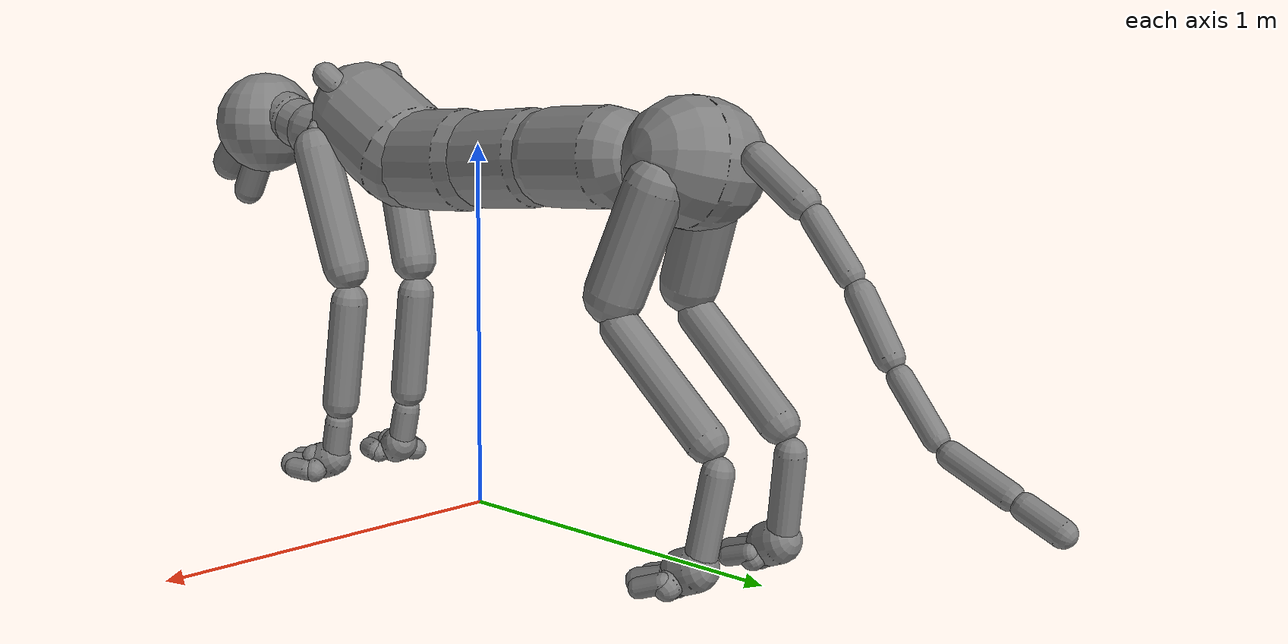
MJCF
<mujoco model="tiger">
  <compiler angle="radian" />
  <option timestep="0.016667" />
  <worldbody>
    <body name="RigPelvis" pos="-3.71397e-09 0.737232 0.989311">
      <geom name="g_RigPelvis" fromto="-0.012497 0.00273413 -0.00190671 -0.0520702 0.0113922 -0.00794469" size="0.163021" density="1540.0" type="capsule" contype="1" conaffinity="1" friction="1.0 0.05 0.05" />
      <body name="RigLBLeg1" pos="0.104141 0.0227845 -0.0158897">
        <joint name="RigLBLeg1_x" type="hinge" axis="1 0 0" pos="0 0 0" range="-1.1186 1.1823" limited="true" armature="0.202781" frictionloss="0.054979" />
        <joint name="RigLBLeg1_y" type="hinge" axis="0 1 0" pos="0 0 0" range="-0.4540 0.7477" limited="true" armature="0.202781" frictionloss="0.054979" />
        <joint name="RigLBLeg1_z" type="hinge" axis="0 0 1" pos="0 0 0" range="-0.4452 0.4915" limited="true" armature="0.202781" frictionloss="0.054979" />
        <geom name="g_RigLBLeg1" fromto="0.00450067 -0.0159535 -0.0412049 0.0330048 -0.116988 -0.302166" size="0.0766259" density="1540.0" type="capsule" contype="1" conaffinity="1" friction="1.0 0.05 0.05" />
        <body name="RigLBLeg2" pos="0.0375057 -0.132944 -0.343369">
          <joint name="RigLBLeg2_x" type="hinge" axis="1 0 0" pos="0 0 0" range="-0.6659 1.8467" limited="true" armature="0.202781" frictionloss="0.054979" />
          <joint name="RigLBLeg2_y" type="hinge" axis="0 1 0" pos="0 0 0" range="-0.1246 0.2644" limited="true" armature="0.202781" frictionloss="0.054979" />
          <joint name="RigLBLeg2_z" type="hinge" axis="0 0 1" pos="0 0 0" range="-0.1422 0.1201" limited="true" armature="0.202781" frictionloss="0.054979" />
          <geom name="g_RigLBLeg2" fromto="-0.00105493 0.04206 -0.0367531 -0.00773596 0.308443 -0.269521" size="0.0517676" density="1540.0" type="capsule" contype="1" conaffinity="1" friction="1.0 0.05 0.05" />
          <body name="RigLBLeg3" pos="-0.00879087 0.350499 -0.306273">
            <joint name="RigLBLeg3_x" type="hinge" axis="1 0 0" pos="0 0 0" range="-1.7965 0.5939" limited="true" armature="0.202781" frictionloss="0.054979" />
            <joint name="RigLBLeg3_y" type="hinge" axis="0 1 0" pos="0 0 0" range="-0.1506 0.2254" limited="true" armature="0.202781" frictionloss="0.054979" />
            <joint name="RigLBLeg3_z" type="hinge" axis="0 0 1" pos="0 0 0" range="-0.2989 0.1909" limited="true" armature="0.202781" frictionloss="0.054979" />
            <geom name="g_RigLBLeg3" fromto="0.00270917 -0.00503764 -0.0313317 0.0198671 -0.0369425 -0.229765" size="0.0399405" density="1540.0" type="capsule" contype="1" conaffinity="1" friction="1.0 0.05 0.05" />
            <body name="RigLBLegAnkle" pos="0.0225769 -0.0419799 -0.2611">
              <joint name="RigLBLegAnkle_x" type="hinge" axis="1 0 0" pos="0 0 0" range="-0.4182 2.2773" limited="true" armature="0.202781" frictionloss="0.054979" />
              <joint name="RigLBLegAnkle_y" type="hinge" axis="0 1 0" pos="0 0 0" range="-0.5642 0.5446" limited="true" armature="0.202781" frictionloss="0.054979" />
              <joint name="RigLBLegAnkle_z" type="hinge" axis="0 0 1" pos="0 0 0" range="-0.9221 1.0499" limited="true" armature="0.202781" frictionloss="0.054979" />
              <geom name="g_RigLBLegAnkle" fromto="0.000560647 -0.00601446 -0.00242466 0.00411145 -0.044106 -0.0177806" size="0.0554814" density="1540.0" type="capsule" contype="1" conaffinity="1" friction="1.0 0.05 0.05" />
              <body name="RigLBLegDigit11" pos="0.0046721 -0.0501207 -0.0202055">
                <joint name="RigLBLegDigit11_x" type="hinge" axis="1 0 0" pos="0 0 0" range="-1.2346 0.8098" limited="true" armature="0.202781" frictionloss="0.054979" />
                <joint name="RigLBLegDigit11_y" type="hinge" axis="0 1 0" pos="0 0 0" range="-0.3347 0.3448" limited="true" armature="0.202781" frictionloss="0.054979" />
                <joint name="RigLBLegDigit11_z" type="hinge" axis="0 0 1" pos="0 0 0" range="-0.4274 0.4434" limited="true" armature="0.202781" frictionloss="0.054979" />
                <geom name="g_RigLBLegDigit11" fromto="0 0 0 -0.0425535 -0.00753521 -0.0275245" size="0.0324687" density="1540.0" type="capsule" contype="1" conaffinity="1" friction="1.0 0.05 0.05" />
                <body name="RigLBLegDigit12" pos="-0.0555421 -0.00783834 -0.0133306">
                  <joint name="RigLBLegDigit12_x" type="hinge" axis="1 0 0" pos="0 0 0" range="-0.4513 1.3530" limited="true" armature="0.202781" frictionloss="0.054979" />
                  <joint name="RigLBLegDigit12_y" type="hinge" axis="0 1 0" pos="0 0 0" range="-0.2023 0.1290" limited="true" armature="0.202781" frictionloss="0.054979" />
                  <joint name="RigLBLegDigit12_z" type="hinge" axis="0 0 1" pos="0 0 0" range="-0.2549 0.1719" limited="true" armature="0.202781" frictionloss="0.054979" />
                  <geom name="g_RigLBLegDigit12" fromto="0 0 0 -0.0040532 -0.064185 -0.0215236" size="0.0248258" density="1540.0" type="capsule" contype="1" conaffinity="1" friction="1.0 0.05 0.05" />
                </body>
              </body>
              <body name="RigLBLegDigit21" pos="0.0046721 -0.0501199 -0.0202055">
                <joint name="RigLBLegDigit21_x" type="hinge" axis="1 0 0" pos="0 0 0" range="-1.2346 0.9774" limited="true" armature="0.202781" frictionloss="0.054979" />
                <joint name="RigLBLegDigit21_y" type="hinge" axis="0 1 0" pos="0 0 0" range="-0.2358 0.1890" limited="true" armature="0.202781" frictionloss="0.054979" />
                <joint name="RigLBLegDigit21_z" type="hinge" axis="0 0 1" pos="0 0 0" range="-0.4272 0.4171" limited="true" armature="0.202781" frictionloss="0.054979" />
                <geom name="g_RigLBLegDigit21" fromto="0 0 0 -0.00578945 -0.0190037 -0.0245509" size="0.0425664" density="1540.0" type="capsule" contype="1" conaffinity="1" friction="1.0 0.05 0.05" />
                <body name="RigLBLegDigit22" pos="-0.0180692 -0.025354 -0.0129026">
                  <joint name="RigLBLegDigit22_x" type="hinge" axis="1 0 0" pos="0 0 0" range="-0.4534 1.3547" limited="true" armature="0.202781" frictionloss="0.054979" />
                  <joint name="RigLBLegDigit22_y" type="hinge" axis="0 1 0" pos="0 0 0" range="-0.1014 0.1248" limited="true" armature="0.202781" frictionloss="0.054979" />
                  <joint name="RigLBLegDigit22_z" type="hinge" axis="0 0 1" pos="0 0 0" range="-0.1390 0.0873" limited="true" armature="0.202781" frictionloss="0.054979" />
                  <geom name="g_RigLBLegDigit22" fromto="0 0 0 0.00536271 -0.077672 -0.022251" size="0.0309904" density="1540.0" type="capsule" contype="1" conaffinity="1" friction="1.0 0.05 0.05" />
                </body>
              </body>
              <body name="RigLBLegDigit31" pos="0.0046721 -0.0501207 -0.0202055">
                <joint name="RigLBLegDigit31_x" type="hinge" axis="1 0 0" pos="0 0 0" range="-1.2346 0.8888" limited="true" armature="0.202781" frictionloss="0.054979" />
                <joint name="RigLBLegDigit31_y" type="hinge" axis="0 1 0" pos="0 0 0" range="-0.1873 0.4675" limited="true" armature="0.202781" frictionloss="0.054979" />
                <joint name="RigLBLegDigit31_z" type="hinge" axis="0 0 1" pos="0 0 0" range="-0.4282 0.4236" limited="true" armature="0.202781" frictionloss="0.054979" />
                <geom name="g_RigLBLegDigit31" fromto="0 0 0 0.0187042 -0.0158245 -0.0222241" size="0.0425943" density="1540.0" type="capsule" contype="1" conaffinity="1" friction="1.0 0.05 0.05" />
                <body name="RigLBLegDigit32" pos="0.0248476 -0.0240667 -0.0124635">
                  <joint name="RigLBLegDigit32_x" type="hinge" axis="1 0 0" pos="0 0 0" range="-0.4477 1.3498" limited="true" armature="0.202781" frictionloss="0.054979" />
                  <joint name="RigLBLegDigit32_y" type="hinge" axis="0 1 0" pos="0 0 0" range="-0.1543 0.2717" limited="true" armature="0.202781" frictionloss="0.054979" />
                  <joint name="RigLBLegDigit32_z" type="hinge" axis="0 0 1" pos="0 0 0" range="-0.2185 0.1205" limited="true" armature="0.202781" frictionloss="0.054979" />
                  <geom name="g_RigLBLegDigit32" fromto="0 0 0 0.0152426 -0.0742541 -0.0210748" size="0.0307951" density="1540.0" type="capsule" contype="1" conaffinity="1" friction="1.0 0.05 0.05" />
                </body>
              </body>
              <body name="RigLBLegDigit41" pos="0.00467202 -0.0501199 -0.0202055">
                <joint name="RigLBLegDigit41_x" type="hinge" axis="1 0 0" pos="0 0 0" range="-1.2346 0.7396" limited="true" armature="0.202781" frictionloss="0.054979" />
                <joint name="RigLBLegDigit41_y" type="hinge" axis="0 1 0" pos="0 0 0" range="-0.1873 0.4945" limited="true" armature="0.202781" frictionloss="0.054979" />
                <joint name="RigLBLegDigit41_z" type="hinge" axis="0 0 1" pos="0 0 0" range="-0.4282 0.4666" limited="true" armature="0.202781" frictionloss="0.054979" />
                <geom name="g_RigLBLegDigit41" fromto="0 0 0 0.0561866 0.00752917 -0.0207512" size="0.0340959" density="1540.0" type="capsule" contype="1" conaffinity="1" friction="1.0 0.05 0.05" />
                <body name="RigLBLegDigit42" pos="0.0658821 0.00318319 -0.0102848">
                  <joint name="RigLBLegDigit42_x" type="hinge" axis="1 0 0" pos="0 0 0" range="-0.4445 1.3470" limited="true" armature="0.202781" frictionloss="0.054979" />
                  <joint name="RigLBLegDigit42_y" type="hinge" axis="0 1 0" pos="0 0 0" range="-0.1704 0.3149" limited="true" armature="0.202781" frictionloss="0.054979" />
                  <joint name="RigLBLegDigit42_z" type="hinge" axis="0 0 1" pos="0 0 0" range="-0.2520 0.2513" limited="true" armature="0.202781" frictionloss="0.054979" />
                  <geom name="g_RigLBLegDigit42" fromto="0 0 0 0.0154778 -0.0625349 -0.023162" size="0.0257556" density="1540.0" type="capsule" contype="1" conaffinity="1" friction="1.0 0.05 0.05" />
                </body>
              </body>
            </body>
          </body>
        </body>
      </body>
      <body name="RigSpine1" pos="-4.10818e-14 -0.204483 6.56961e-08">
        <joint name="RigSpine1_x" type="hinge" axis="1 0 0" pos="0 0 0" range="-0.4792 0.4654" limited="true" armature="0.202781" frictionloss="0.054979" />
        <joint name="RigSpine1_y" type="hinge" axis="0 1 0" pos="0 0 0" range="-0.2512 0.2512" limited="true" armature="0.202781" frictionloss="0.054979" />
        <joint name="RigSpine1_z" type="hinge" axis="0 0 1" pos="0 0 0" range="-0.2732 0.3115" limited="true" armature="0.202781" frictionloss="0.054979" />
        <geom name="g_RigSpine1" fromto="-3.13256e-09 -0.0324054 -0.001533 -2.29722e-08 -0.237635 -0.0112424" size="0.130527" density="1540.0" type="capsule" contype="1" conaffinity="1" friction="1.0 0.05 0.05" />
        <body name="RigSpine2" pos="-2.6104e-08 -0.270047 -0.0127751">
          <joint name="RigSpine2_x" type="hinge" axis="1 0 0" pos="0 0 0" range="-0.3832 0.4203" limited="true" armature="0.202781" frictionloss="0.054979" />
          <joint name="RigSpine2_y" type="hinge" axis="0 1 0" pos="0 0 0" range="-0.3709 0.3709" limited="true" armature="0.202781" frictionloss="0.054979" />
          <joint name="RigSpine2_z" type="hinge" axis="0 0 1" pos="0 0 0" range="-0.3928 0.3904" limited="true" armature="0.202781" frictionloss="0.054979" />
          <geom name="g_RigSpine2" fromto="-2.03054e-09 -0.0323555 -0.00236482 -1.48908e-08 -0.237274 -0.0173424" size="0.13139" density="1000.0" type="capsule" contype="1" conaffinity="1" friction="1.0 0.05 0.05" />
          <body name="RigSpine3" pos="-1.69213e-08 -0.269624 -0.0197069">
            <joint name="RigSpine3_x" type="hinge" axis="1 0 0" pos="0 0 0" range="-0.2325 0.4305" limited="true" armature="0.202781" frictionloss="0.054979" />
            <joint name="RigSpine3_y" type="hinge" axis="0 1 0" pos="0 0 0" range="-0.3755 0.3755" limited="true" armature="0.202781" frictionloss="0.054979" />
            <joint name="RigSpine3_z" type="hinge" axis="0 0 1" pos="0 0 0" range="-0.4491 0.4485" limited="true" armature="0.202781" frictionloss="0.054979" />
            <geom name="g_RigSpine3" fromto="7.46807e-09 -0.0324054 -0.00153378 5.47654e-08 -0.237635 -0.0112476" size="0.140864" density="1000.0" type="capsule" contype="1" conaffinity="1" friction="1.0 0.05 0.05" />
            <body name="RigChest" pos="6.22336e-08 -0.270047 -0.012782">
              <joint name="RigChest_x" type="hinge" axis="1 0 0" pos="0 0 0" range="-0.3344 0.4872" limited="true" armature="0.202781" frictionloss="0.054979" />
              <joint name="RigChest_y" type="hinge" axis="0 1 0" pos="0 0 0" range="-0.2445 0.2445" limited="true" armature="0.202781" frictionloss="0.054979" />
              <joint name="RigChest_z" type="hinge" axis="0 0 1" pos="0 0 0" range="-0.3529 0.3529" limited="true" armature="0.202781" frictionloss="0.054979" />
              <geom name="g_RigChest" fromto="-1.76575e-10 -0.0301382 0.0164624 -1.29491e-09 -0.221008 0.120725" size="0.155617" density="1000.0" type="capsule" contype="1" conaffinity="1" friction="1.0 0.05 0.05" />
              <body name="RigNeck1" pos="-1.53739e-08 -0.294347 0.0522614">
                <joint name="RigNeck1_x" type="hinge" axis="1 0 0" pos="0 0 0" range="-0.6511 0.5810" limited="true" armature="0.202781" frictionloss="0.054979" />
                <joint name="RigNeck1_y" type="hinge" axis="0 1 0" pos="0 0 0" range="-0.1951 0.2132" limited="true" armature="0.202781" frictionloss="0.054979" />
                <joint name="RigNeck1_z" type="hinge" axis="0 0 1" pos="0 0 0" range="-0.4523 0.8165" limited="true" armature="0.202781" frictionloss="0.054979" />
                <geom name="g_RigNeck1" fromto="-2.93951e-08 -0.0111434 4.86388e-06 -2.15557e-07 -0.0817158 3.56681e-05" size="0.0867253" density="1000.0" type="capsule" contype="1" conaffinity="1" friction="1.0 0.05 0.05" />
                <body name="RigNeck2" pos="-2.44955e-07 -0.09286 4.05325e-05">
                  <joint name="RigNeck2_x" type="hinge" axis="1 0 0" pos="0 0 0" range="-0.3444 0.5429" limited="true" armature="0.202781" frictionloss="0.054979" />
                  <joint name="RigNeck2_y" type="hinge" axis="0 1 0" pos="0 0 0" range="-0.2646 0.2646" limited="true" armature="0.202781" frictionloss="0.054979" />
                  <joint name="RigNeck2_z" type="hinge" axis="0 0 1" pos="0 0 0" range="-0.3602 0.3770" limited="true" armature="0.202781" frictionloss="0.054979" />
                  <geom name="g_RigNeck2" fromto="-2.73181e-08 -0.0111167 0.00173338 -2.00333e-07 -0.0815255 0.0127114" size="0.0867253" density="1000.0" type="capsule" contype="1" conaffinity="1" friction="1.0 0.05 0.05" />
                  <body name="RigNeck3" pos="-2.27655e-07 -0.0926448 0.0144448">
                    <joint name="RigNeck3_x" type="hinge" axis="1 0 0" pos="0 0 0" range="-0.3421 0.4979" limited="true" armature="0.202781" frictionloss="0.054979" />
                    <joint name="RigNeck3_y" type="hinge" axis="0 1 0" pos="0 0 0" range="-0.2145 0.2145" limited="true" armature="0.202781" frictionloss="0.054979" />
                    <joint name="RigNeck3_z" type="hinge" axis="0 0 1" pos="0 0 0" range="-0.2979 0.2867" limited="true" armature="0.202781" frictionloss="0.054979" />
                    <geom name="g_RigNeck3" fromto="-2.63812e-08 -0.0113104 0.00322582 -1.93461e-07 -0.0829403 0.0236559" size="0.0761227" density="1000.0" type="capsule" contype="1" conaffinity="1" friction="1.0 0.05 0.05" />
                    <body name="RigNeck4" pos="-2.19846e-07 -0.0942467 0.0268816">
                      <joint name="RigNeck4_x" type="hinge" axis="1 0 0" pos="0 0 0" range="-0.7504 0.5229" limited="true" armature="0.202781" frictionloss="0.054979" />
                      <joint name="RigNeck4_y" type="hinge" axis="0 1 0" pos="0 0 0" range="-0.3846 0.3846" limited="true" armature="0.202781" frictionloss="0.054979" />
                      <joint name="RigNeck4_z" type="hinge" axis="0 0 1" pos="0 0 0" range="-0.4534 0.4534" limited="true" armature="0.202781" frictionloss="0.054979" />
                      <geom name="g_RigNeck4" fromto="3.32665e-07 -0.00992668 0.00276988 2.43955e-06 -0.0727932 0.0203123" size="0.0774232" density="1000.0" type="capsule" contype="1" conaffinity="1" friction="1.0 0.05 0.05" />
                      <body name="RigHead" pos="2.7722e-06 -0.0827199 0.0230824">
                        <joint name="RigHead_x" type="hinge" axis="1 0 0" pos="0 0 0" range="-0.8230 0.5439" limited="true" armature="0.202781" frictionloss="0.054979" />
                        <joint name="RigHead_y" type="hinge" axis="0 1 0" pos="0 0 0" range="-0.3970 0.3970" limited="true" armature="0.202781" frictionloss="0.054979" />
                        <joint name="RigHead_z" type="hinge" axis="0 0 1" pos="0 0 0" range="-0.5157 0.5157" limited="true" armature="0.202781" frictionloss="0.054979" />
                        <geom name="g_RigHead" type="sphere" pos="-2.07987e-06 -0.0685405 -0.0323949" size="0.155221" density="838.9" contype="1" conaffinity="1" friction="1.0 0.05 0.05" />
                        <geom name="g_RigHead_snout" fromto="-2.07987e-06 -0.102943 0.00386742 -2.07987e-06 -0.27134 -0.164529" size="0.0604372" density="838.9" type="capsule" contype="1" conaffinity="1" friction="1.0 0.05 0.05" />
                        <body name="RigJaw1" pos="-2.72071e-08 -0.0387069 -0.0701419">
                          <joint name="RigJaw1_x" type="hinge" axis="1 0 0" pos="0 0 0" range="-0.4014 0.6986" limited="true" armature="0.202781" frictionloss="0.054979" />
                          <joint name="RigJaw1_y" type="hinge" axis="0 1 0" pos="0 0 0" range="-0.1388 0.1388" limited="true" armature="0.202781" frictionloss="0.054979" />
                          <joint name="RigJaw1_z" type="hinge" axis="0 0 1" pos="0 0 0" range="-0.1091 0.1091" limited="true" armature="0.202781" frictionloss="0.054979" />
                          <geom name="g_RigJaw1" fromto="-2.05266e-06 -0.0642367 -0.0608122 -2.05266e-06 -0.138701 -0.179979" size="0.0464902" density="838.9" type="capsule" contype="1" conaffinity="1" friction="1.0 0.05 0.05" />
                        </body>
                      </body>
                    </body>
                  </body>
                </body>
              </body>
              <body name="RigLFLegCollarbone" pos="-0.0347003 -0.277805 0.126769">
                <joint name="RigLFLegCollarbone_x" type="hinge" axis="1 0 0" pos="0 0 0" range="-0.2925 0.2681" limited="true" armature="0.202781" frictionloss="0.054979" />
                <joint name="RigLFLegCollarbone_y" type="hinge" axis="0 1 0" pos="0 0 0" range="-0.2371 0.6865" limited="true" armature="0.202781" frictionloss="0.054979" />
                <joint name="RigLFLegCollarbone_z" type="hinge" axis="0 0 1" pos="0 0 0" range="-0.4193 0.3521" limited="true" armature="0.202781" frictionloss="0.054979" />
                <geom name="g_RigLFLegCollarbone" fromto="0.022087 6.21148e-06 -0.00618755 0.161971 4.55509e-05 -0.0453752" size="0.0297135" density="1000.5" type="capsule" contype="1" conaffinity="1" friction="1.0 0.05 0.05" />
                <body name="RigLFLeg1" pos="0.184058 5.17627e-05 -0.051563">
                  <joint name="RigLFLeg1_x" type="hinge" axis="1 0 0" pos="0 0 0" range="-0.6847 0.9281" limited="true" armature="0.202781" frictionloss="0.054979" />
                  <joint name="RigLFLeg1_y" type="hinge" axis="0 1 0" pos="0 0 0" range="-0.8833 0.4380" limited="true" armature="0.202781" frictionloss="0.054979" />
                  <joint name="RigLFLeg1_z" type="hinge" axis="0 0 1" pos="0 0 0" range="-0.5692 0.5046" limited="true" armature="0.202781" frictionloss="0.054979" />
                  <geom name="g_RigLFLeg1" fromto="-0.00311543 0.0165338 -0.0525524 -0.0228465 0.12125 -0.385381" size="0.0660645" density="1000.5" type="capsule" contype="1" conaffinity="1" friction="1.0 0.05 0.05" />
                  <body name="RigLFLeg2" pos="-0.0259619 0.137783 -0.437934">
                    <joint name="RigLFLeg2_x" type="hinge" axis="1 0 0" pos="0 0 0" range="-1.9085 0.4150" limited="true" armature="0.202781" frictionloss="0.054979" />
                    <joint name="RigLFLeg2_y" type="hinge" axis="0 1 0" pos="0 0 0" range="-0.2753 0.1353" limited="true" armature="0.202781" frictionloss="0.054979" />
                    <joint name="RigLFLeg2_z" type="hinge" axis="0 0 1" pos="0 0 0" range="-0.2342 0.1285" limited="true" armature="0.202781" frictionloss="0.054979" />
                    <geom name="g_RigLFLeg2" fromto="0.000570525 -0.00708669 -0.04754 0.00418386 -0.0519686 -0.34863" size="0.0533189" density="1000.5" type="capsule" contype="1" conaffinity="1" friction="1.0 0.05 0.05" />
                    <body name="RigLFLeg3" pos="0.00475435 -0.0590554 -0.396171">
                      <joint name="RigLFLeg3_x" type="hinge" axis="1 0 0" pos="0 0 0" range="-0.3454 2.3444" limited="true" armature="0.202781" frictionloss="0.054979" />
                      <joint name="RigLFLeg3_y" type="hinge" axis="0 1 0" pos="0 0 0" range="-0.2482 0.8543" limited="true" armature="0.202781" frictionloss="0.054979" />
                      <joint name="RigLFLeg3_z" type="hinge" axis="0 0 1" pos="0 0 0" range="-0.3979 0.8034" limited="true" armature="0.202781" frictionloss="0.054979" />
                      <geom name="g_RigLFLeg3" fromto="-0.000264398 -0.00367686 -0.0150734 -0.00193892 -0.0269634 -0.110538" size="0.0404029" density="1000.5" type="capsule" contype="1" conaffinity="1" friction="1.0 0.05 0.05" />
                      <body name="RigLFLegAnkle" pos="-0.00220336 -0.0306402 -0.125607">
                        <joint name="RigLFLegAnkle_x" type="hinge" axis="1 0 0" pos="0 0 0" range="-0.3116 2.0357" limited="true" armature="0.202781" frictionloss="0.054979" />
                        <joint name="RigLFLegAnkle_y" type="hinge" axis="0 1 0" pos="0 0 0" range="-0.4435 1.0126" limited="true" armature="0.202781" frictionloss="0.054979" />
                        <joint name="RigLFLegAnkle_z" type="hinge" axis="0 0 1" pos="0 0 0" range="-0.8155 0.7421" limited="true" armature="0.202781" frictionloss="0.054979" />
                        <geom name="g_RigLFLegAnkle" fromto="0.00196544 -0.00590071 -0.00230652 0.0144138 -0.0432724 -0.0169144" size="0.0529802" density="1000.5" type="capsule" contype="1" conaffinity="1" friction="1.0 0.05 0.05" />
                        <body name="RigLFLegDigit11" pos="0.0163788 -0.0491726 -0.0192196">
                          <joint name="RigLFLegDigit11_x" type="hinge" axis="1 0 0" pos="0 0 0" range="-1.8232 0.4278" limited="true" armature="0.202781" frictionloss="0.054979" />
                          <joint name="RigLFLegDigit11_y" type="hinge" axis="0 1 0" pos="0 0 0" range="-0.6347 0.5256" limited="true" armature="0.202781" frictionloss="0.054979" />
                          <joint name="RigLFLegDigit11_z" type="hinge" axis="0 0 1" pos="0 0 0" range="-0.4580 0.1848" limited="true" armature="0.202781" frictionloss="0.054979" />
                          <geom name="g_RigLFLegDigit11" fromto="0 0 0 -0.0507717 -0.0140045 -0.0140357" size="0.0310182" density="1000.5" type="capsule" contype="1" conaffinity="1" friction="1.0 0.05 0.05" />
                          <body name="RigLFLegDigit12" pos="-0.0560544 -0.0222669 -0.0107197">
                            <joint name="RigLFLegDigit12_x" type="hinge" axis="1 0 0" pos="0 0 0" range="-0.3822 2.8648" limited="true" armature="0.202781" frictionloss="0.054979" />
                            <joint name="RigLFLegDigit12_y" type="hinge" axis="0 1 0" pos="0 0 0" range="-0.3298 0.7237" limited="true" armature="0.202781" frictionloss="0.054979" />
                            <joint name="RigLFLegDigit12_z" type="hinge" axis="0 0 1" pos="0 0 0" range="-0.5305 0.4206" limited="true" armature="0.202781" frictionloss="0.054979" />
                            <geom name="g_RigLFLegDigit12" fromto="0 0 0 0.0113395 -0.0476826 0.000772613" size="0.0308695" density="1000.5" type="capsule" contype="1" conaffinity="1" friction="1.0 0.05 0.05" />
                          </body>
                        </body>
                        <body name="RigLFLegDigit21" pos="0.0163788 -0.0491726 -0.0192196">
                          <joint name="RigLFLegDigit21_x" type="hinge" axis="1 0 0" pos="0 0 0" range="-1.8151 0.4265" limited="true" armature="0.202781" frictionloss="0.054979" />
                          <joint name="RigLFLegDigit21_y" type="hinge" axis="0 1 0" pos="0 0 0" range="-0.5857 0.1982" limited="true" armature="0.202781" frictionloss="0.054979" />
                          <joint name="RigLFLegDigit21_z" type="hinge" axis="0 0 1" pos="0 0 0" range="-0.4576 0.1594" limited="true" armature="0.202781" frictionloss="0.054979" />
                          <geom name="g_RigLFLegDigit21" fromto="0 0 0 -0.0101205 -0.0102738 0.0141711" size="0.039247" density="1000.5" type="capsule" contype="1" conaffinity="1" friction="1.0 0.05 0.05" />
                          <body name="RigLFLegDigit22" pos="-0.0139428 -0.0234019 -0.00987414">
                            <joint name="RigLFLegDigit22_x" type="hinge" axis="1 0 0" pos="0 0 0" range="-0.3980 2.8730" limited="true" armature="0.202781" frictionloss="0.054979" />
                            <joint name="RigLFLegDigit22_y" type="hinge" axis="0 1 0" pos="0 0 0" range="-0.1984 0.6366" limited="true" armature="0.202781" frictionloss="0.054979" />
                            <joint name="RigLFLegDigit22_z" type="hinge" axis="0 0 1" pos="0 0 0" range="-0.5772 0.2824" limited="true" armature="0.202781" frictionloss="0.054979" />
                            <geom name="g_RigLFLegDigit22" fromto="0 0 0 0.0135018 -0.066047 0.000842824" size="0.0363274" density="1000.5" type="capsule" contype="1" conaffinity="1" friction="1.0 0.05 0.05" />
                          </body>
                        </body>
                        <body name="RigLFLegDigit31" pos="0.0163797 -0.0491726 -0.0192239">
                          <joint name="RigLFLegDigit31_x" type="hinge" axis="1 0 0" pos="0 0 0" range="-1.8151 0.4265" limited="true" armature="0.202781" frictionloss="0.054979" />
                          <joint name="RigLFLegDigit31_y" type="hinge" axis="0 1 0" pos="0 0 0" range="-0.4083 0.1982" limited="true" armature="0.202781" frictionloss="0.054979" />
                          <joint name="RigLFLegDigit31_z" type="hinge" axis="0 0 1" pos="0 0 0" range="-0.4589 0.1594" limited="true" armature="0.202781" frictionloss="0.054979" />
                          <geom name="g_RigLFLegDigit31" fromto="0 0 0 0.0166381 -0.00115699 0.0135998" size="0.0408463" density="1000.5" type="capsule" contype="1" conaffinity="1" friction="1.0 0.05 0.05" />
                          <body name="RigLFLegDigit32" pos="0.0307556 -0.00640126 -0.0100756">
                            <joint name="RigLFLegDigit32_x" type="hinge" axis="1 0 0" pos="0 0 0" range="-0.3736 2.8802" limited="true" armature="0.202781" frictionloss="0.054979" />
                            <joint name="RigLFLegDigit32_y" type="hinge" axis="0 1 0" pos="0 0 0" range="-0.1601 0.7878" limited="true" armature="0.202781" frictionloss="0.054979" />
                            <joint name="RigLFLegDigit32_z" type="hinge" axis="0 0 1" pos="0 0 0" range="-0.7127 0.2741" limited="true" armature="0.202781" frictionloss="0.054979" />
                            <geom name="g_RigLFLegDigit32" fromto="0 0 0 0.0201025 -0.0608005 -0.00113838" size="0.0363553" density="1000.5" type="capsule" contype="1" conaffinity="1" friction="1.0 0.05 0.05" />
                          </body>
                        </body>
                        <body name="RigLFLegDigit41" pos="0.0163788 -0.0491726 -0.0192196">
                          <joint name="RigLFLegDigit41_x" type="hinge" axis="1 0 0" pos="0 0 0" range="-1.8203 0.4265" limited="true" armature="0.202781" frictionloss="0.054979" />
                          <joint name="RigLFLegDigit41_y" type="hinge" axis="0 1 0" pos="0 0 0" range="-0.4083 0.1982" limited="true" armature="0.202781" frictionloss="0.054979" />
                          <joint name="RigLFLegDigit41_z" type="hinge" axis="0 0 1" pos="0 0 0" range="-0.4620 0.1594" limited="true" armature="0.202781" frictionloss="0.054979" />
                          <geom name="g_RigLFLegDigit41" fromto="0 0 0 0.0489029 0.0399905 -0.0131114" size="0.0325989" density="1000.5" type="capsule" contype="1" conaffinity="1" friction="1.0 0.05 0.05" />
                          <body name="RigLFLegDigit42" pos="0.0623284 0.0232925 -0.0126951">
                            <joint name="RigLFLegDigit42_x" type="hinge" axis="1 0 0" pos="0 0 0" range="-0.3282 2.8916" limited="true" armature="0.202781" frictionloss="0.054979" />
                            <joint name="RigLFLegDigit42_y" type="hinge" axis="0 1 0" pos="0 0 0" range="-0.1784 0.8231" limited="true" armature="0.202781" frictionloss="0.054979" />
                            <joint name="RigLFLegDigit42_z" type="hinge" axis="0 0 1" pos="0 0 0" range="-0.9001 0.2935" limited="true" armature="0.202781" frictionloss="0.054979" />
                            <geom name="g_RigLFLegDigit42" fromto="0 0 0 0.0124786 -0.0487053 0.00214576" size="0.0296328" density="1000.5" type="capsule" contype="1" conaffinity="1" friction="1.0 0.05 0.05" />
                          </body>
                        </body>
                      </body>
                    </body>
                  </body>
                </body>
              </body>
              <body name="RigRFLegCollarbone" pos="0.0347011 -0.277805 0.126769">
                <joint name="RigRFLegCollarbone_x" type="hinge" axis="1 0 0" pos="0 0 0" range="-0.2925 0.2681" limited="true" armature="0.202781" frictionloss="0.054979" />
                <joint name="RigRFLegCollarbone_y" type="hinge" axis="0 1 0" pos="0 0 0" range="-0.6865 0.2371" limited="true" armature="0.202781" frictionloss="0.054979" />
                <joint name="RigRFLegCollarbone_z" type="hinge" axis="0 0 1" pos="0 0 0" range="-0.3521 0.4193" limited="true" armature="0.202781" frictionloss="0.054979" />
                <geom name="g_RigRFLegCollarbone" fromto="-0.022087 6.18134e-06 -0.00618728 -0.161971 4.53304e-05 -0.0453735" size="0.0297135" density="1000.5" type="capsule" contype="1" conaffinity="1" friction="1.0 0.05 0.05" />
                <body name="RigRFLeg1" pos="-0.184058 5.15113e-05 -0.0515612">
                  <joint name="RigRFLeg1_x" type="hinge" axis="1 0 0" pos="0 0 0" range="-0.6847 0.9281" limited="true" armature="0.202781" frictionloss="0.054979" />
                  <joint name="RigRFLeg1_y" type="hinge" axis="0 1 0" pos="0 0 0" range="-0.4380 0.8833" limited="true" armature="0.202781" frictionloss="0.054979" />
                  <joint name="RigRFLeg1_z" type="hinge" axis="0 0 1" pos="0 0 0" range="-0.5046 0.5692" limited="true" armature="0.202781" frictionloss="0.054979" />
                  <geom name="g_RigRFLeg1" fromto="0.0030896 0.0165373 -0.0525524 0.022657 0.121276 -0.385381" size="0.0660829" density="1000.5" type="capsule" contype="1" conaffinity="1" friction="1.0 0.05 0.05" />
                  <body name="RigRFLeg2" pos="0.0257466 0.137809 -0.437934">
                    <joint name="RigRFLeg2_x" type="hinge" axis="1 0 0" pos="0 0 0" range="-1.9085 0.4150" limited="true" armature="0.202781" frictionloss="0.054979" />
                    <joint name="RigRFLeg2_y" type="hinge" axis="0 1 0" pos="0 0 0" range="-0.1353 0.2753" limited="true" armature="0.202781" frictionloss="0.054979" />
                    <joint name="RigRFLeg2_z" type="hinge" axis="0 0 1" pos="0 0 0" range="-0.1285 0.2342" limited="true" armature="0.202781" frictionloss="0.054979" />
                    <geom name="g_RigRFLeg2" fromto="-0.000551692 -0.0070891 -0.04754 -0.00404575 -0.0519866 -0.34863" size="0.0533189" density="1000.5" type="capsule" contype="1" conaffinity="1" friction="1.0 0.05 0.05" />
                    <body name="RigRFLeg3" pos="-0.00459745 -0.059076 -0.396162">
                      <joint name="RigRFLeg3_x" type="hinge" axis="1 0 0" pos="0 0 0" range="-0.3622 2.3392" limited="true" armature="0.202781" frictionloss="0.054979" />
                      <joint name="RigRFLeg3_y" type="hinge" axis="0 1 0" pos="0 0 0" range="-0.8543 0.2375" limited="true" armature="0.202781" frictionloss="0.054979" />
                      <joint name="RigRFLeg3_z" type="hinge" axis="0 0 1" pos="0 0 0" range="-0.8253 0.4073" limited="true" armature="0.202781" frictionloss="0.054979" />
                      <geom name="g_RigRFLeg3" fromto="0.00027585 -0.00367884 -0.0150726 0.00202287 -0.026978 -0.110529" size="0.0403968" density="1000.5" type="capsule" contype="1" conaffinity="1" friction="1.0 0.05 0.05" />
                      <body name="RigRFLegAnkle" pos="0.00229877 -0.0306566 -0.125599">
                        <joint name="RigRFLegAnkle_x" type="hinge" axis="1 0 0" pos="0 0 0" range="-0.3116 2.0267" limited="true" armature="0.202781" frictionloss="0.054979" />
                        <joint name="RigRFLegAnkle_y" type="hinge" axis="0 1 0" pos="0 0 0" range="-0.9493 0.4306" limited="true" armature="0.202781" frictionloss="0.054979" />
                        <joint name="RigRFLegAnkle_z" type="hinge" axis="0 0 1" pos="0 0 0" range="-0.7768 0.8115" limited="true" armature="0.202781" frictionloss="0.054979" />
                        <geom name="g_RigRFLegAnkle" fromto="-0.00196759 -0.00589994 -0.00230669 -0.0144293 -0.0432664 -0.0169153" size="0.0529895" density="1000.5" type="capsule" contype="1" conaffinity="1" friction="1.0 0.05 0.05" />
                        <body name="RigRFLegDigit11" pos="-0.0163969 -0.0491666 -0.0192213">
                          <joint name="RigRFLegDigit11_x" type="hinge" axis="1 0 0" pos="0 0 0" range="-1.8232 0.4278" limited="true" armature="0.202781" frictionloss="0.054979" />
                          <joint name="RigRFLegDigit11_y" type="hinge" axis="0 1 0" pos="0 0 0" range="-0.5256 0.6346" limited="true" armature="0.202781" frictionloss="0.054979" />
                          <joint name="RigRFLegDigit11_z" type="hinge" axis="0 0 1" pos="0 0 0" range="-0.1848 0.4580" limited="true" armature="0.202781" frictionloss="0.054979" />
                          <geom name="g_RigRFLegDigit11" fromto="0 0 0 0.0507177 -0.0139983 -0.0140286" size="0.0310275" density="1000.5" type="capsule" contype="1" conaffinity="1" friction="1.0 0.05 0.05" />
                          <body name="RigRFLegDigit12" pos="0.0560544 -0.0222669 -0.0107197">
                            <joint name="RigRFLegDigit12_x" type="hinge" axis="1 0 0" pos="0 0 0" range="-0.3752 2.8290" limited="true" armature="0.202781" frictionloss="0.054979" />
                            <joint name="RigRFLegDigit12_y" type="hinge" axis="0 1 0" pos="0 0 0" range="-0.7024 0.3298" limited="true" armature="0.202781" frictionloss="0.054979" />
                            <joint name="RigRFLegDigit12_z" type="hinge" axis="0 0 1" pos="0 0 0" range="-0.3150 0.5212" limited="true" armature="0.202781" frictionloss="0.054979" />
                            <geom name="g_RigRFLegDigit12" fromto="0 0 0 -0.0113653 -0.0476915 0.000754398" size="0.0308602" density="1000.5" type="capsule" contype="1" conaffinity="1" friction="1.0 0.05 0.05" />
                          </body>
                        </body>
                        <body name="RigRFLegDigit21" pos="-0.0163969 -0.0491666 -0.0192213">
                          <joint name="RigRFLegDigit21_x" type="hinge" axis="1 0 0" pos="0 0 0" range="-1.8151 0.4261" limited="true" armature="0.202781" frictionloss="0.054979" />
                          <joint name="RigRFLegDigit21_y" type="hinge" axis="0 1 0" pos="0 0 0" range="-0.1980 0.5856" limited="true" armature="0.202781" frictionloss="0.054979" />
                          <joint name="RigRFLegDigit21_z" type="hinge" axis="0 0 1" pos="0 0 0" range="-0.1594 0.4576" limited="true" armature="0.202781" frictionloss="0.054979" />
                          <geom name="g_RigRFLegDigit21" fromto="0 0 0 0.010102 -0.0102739 0.0141552" size="0.0392377" density="1000.5" type="capsule" contype="1" conaffinity="1" friction="1.0 0.05 0.05" />
                          <body name="RigRFLegDigit22" pos="0.0139428 -0.0234019 -0.00987414">
                            <joint name="RigRFLegDigit22_x" type="hinge" axis="1 0 0" pos="0 0 0" range="-0.3075 2.8406" limited="true" armature="0.202781" frictionloss="0.054979" />
                            <joint name="RigRFLegDigit22_y" type="hinge" axis="0 1 0" pos="0 0 0" range="-0.6231 0.1982" limited="true" armature="0.202781" frictionloss="0.054979" />
                            <joint name="RigRFLegDigit22_z" type="hinge" axis="0 0 1" pos="0 0 0" range="-0.2690 0.5772" limited="true" armature="0.202781" frictionloss="0.054979" />
                            <geom name="g_RigRFLegDigit22" fromto="0 0 0 -0.013506 -0.0660451 0.000845787" size="0.0363181" density="1000.5" type="capsule" contype="1" conaffinity="1" friction="1.0 0.05 0.05" />
                          </body>
                        </body>
                        <body name="RigRFLegDigit31" pos="-0.0163969 -0.0491666 -0.0192255">
                          <joint name="RigRFLegDigit31_x" type="hinge" axis="1 0 0" pos="0 0 0" range="-1.8151 0.4261" limited="true" armature="0.202781" frictionloss="0.054979" />
                          <joint name="RigRFLegDigit31_y" type="hinge" axis="0 1 0" pos="0 0 0" range="-0.1980 0.4091" limited="true" armature="0.202781" frictionloss="0.054979" />
                          <joint name="RigRFLegDigit31_z" type="hinge" axis="0 0 1" pos="0 0 0" range="-0.1594 0.4589" limited="true" armature="0.202781" frictionloss="0.054979" />
                          <geom name="g_RigRFLegDigit31" fromto="0 0 0 -0.0166511 -0.00114627 0.013603" size="0.0408556" density="1000.5" type="capsule" contype="1" conaffinity="1" friction="1.0 0.05 0.05" />
                          <body name="RigRFLegDigit32" pos="-0.0307556 -0.00640126 -0.0100756">
                            <joint name="RigRFLegDigit32_x" type="hinge" axis="1 0 0" pos="0 0 0" range="-0.3115 2.8429" limited="true" armature="0.202781" frictionloss="0.054979" />
                            <joint name="RigRFLegDigit32_y" type="hinge" axis="0 1 0" pos="0 0 0" range="-0.7734 0.1653" limited="true" armature="0.202781" frictionloss="0.054979" />
                            <joint name="RigRFLegDigit32_z" type="hinge" axis="0 0 1" pos="0 0 0" range="-0.2705 0.7127" limited="true" armature="0.202781" frictionloss="0.054979" />
                            <geom name="g_RigRFLegDigit32" fromto="0 0 0 -0.0201238 -0.0608079 -0.00114573" size="0.0363367" density="1000.5" type="capsule" contype="1" conaffinity="1" friction="1.0 0.05 0.05" />
                          </body>
                        </body>
                        <body name="RigRFLegDigit41" pos="-0.0163969 -0.0491666 -0.0192213">
                          <joint name="RigRFLegDigit41_x" type="hinge" axis="1 0 0" pos="0 0 0" range="-1.8203 0.4261" limited="true" armature="0.202781" frictionloss="0.054979" />
                          <joint name="RigRFLegDigit41_y" type="hinge" axis="0 1 0" pos="0 0 0" range="-0.1980 0.4091" limited="true" armature="0.202781" frictionloss="0.054979" />
                          <joint name="RigRFLegDigit41_z" type="hinge" axis="0 0 1" pos="0 0 0" range="-0.1594 0.4613" limited="true" armature="0.202781" frictionloss="0.054979" />
                          <geom name="g_RigRFLegDigit41" fromto="0 0 0 -0.0489655 0.0400147 -0.0131394" size="0.0325989" density="1000.5" type="capsule" contype="1" conaffinity="1" friction="1.0 0.05 0.05" />
                          <body name="RigRFLegDigit42" pos="-0.0623284 0.0232925 -0.0126951">
                            <joint name="RigRFLegDigit42_x" type="hinge" axis="1 0 0" pos="0 0 0" range="-0.3282 2.8430" limited="true" armature="0.202781" frictionloss="0.054979" />
                            <joint name="RigRFLegDigit42_y" type="hinge" axis="0 1 0" pos="0 0 0" range="-0.8099 0.1769" limited="true" armature="0.202781" frictionloss="0.054979" />
                            <joint name="RigRFLegDigit42_z" type="hinge" axis="0 0 1" pos="0 0 0" range="-0.2779 0.8978" limited="true" armature="0.202781" frictionloss="0.054979" />
                            <geom name="g_RigRFLegDigit42" fromto="0 0 0 -0.012494 -0.0487331 0.0021439" size="0.0296235" density="1000.5" type="capsule" contype="1" conaffinity="1" friction="1.0 0.05 0.05" />
                          </body>
                        </body>
                      </body>
                    </body>
                  </body>
                </body>
              </body>
              <body name="RigLShoulderBlade1" pos="-0.09224 -0.202891 0.190069">
                <joint name="RigLShoulderBlade1_x" type="hinge" axis="1 0 0" pos="0 0 0" range="-0.2891 0.1272" limited="true" armature="0.202781" frictionloss="0.054979" />
                <joint name="RigLShoulderBlade1_y" type="hinge" axis="0 1 0" pos="0 0 0" range="-0.3652 0.3652" limited="true" armature="0.202781" frictionloss="0.054979" />
                <joint name="RigLShoulderBlade1_z" type="hinge" axis="0 0 1" pos="0 0 0" range="-0.2868 0.2868" limited="true" armature="0.202781" frictionloss="0.054979" />
                <geom name="g_RigLShoulderBlade1" fromto="-0.0066416 -0.0146084 0.0136845 -0.0223969 -0.0492628 0.0461465" size="0.038663" density="1000.0" type="capsule" contype="1" conaffinity="1" friction="1.0 0.05 0.05" />
              </body>
              <body name="RigRShoulderBlade1" pos="0.09224 -0.202891 0.190069">
                <joint name="RigRShoulderBlade1_x" type="hinge" axis="1 0 0" pos="0 0 0" range="-0.2891 0.1272" limited="true" armature="0.202781" frictionloss="0.054979" />
                <joint name="RigRShoulderBlade1_y" type="hinge" axis="0 1 0" pos="0 0 0" range="-0.3652 0.3652" limited="true" armature="0.202781" frictionloss="0.054979" />
                <joint name="RigRShoulderBlade1_z" type="hinge" axis="0 0 1" pos="0 0 0" range="-0.2868 0.2868" limited="true" armature="0.202781" frictionloss="0.054979" />
                <geom name="g_RigRShoulderBlade1" fromto="0.0066416 -0.0146084 0.0136845 0.0223969 -0.0492628 0.0461465" size="0.038663" density="1000.0" type="capsule" contype="1" conaffinity="1" friction="1.0 0.05 0.05" />
              </body>
            </body>
          </body>
        </body>
      </body>
      <body name="RigTail1" pos="-2.98816e-08 0.209323 0.0280113">
        <joint name="RigTail1_x" type="hinge" axis="1 0 0" pos="0 0 0" range="-0.6451 1.6456" limited="true" armature="0.202781" frictionloss="0.054979" />
        <joint name="RigTail1_y" type="hinge" axis="0 1 0" pos="0 0 0" range="-0.3564 0.3564" limited="true" armature="0.202781" frictionloss="0.054979" />
        <joint name="RigTail1_z" type="hinge" axis="0 0 1" pos="0 0 0" range="-0.5003 0.5003" limited="true" armature="0.202781" frictionloss="0.054979" />
        <geom name="g_RigTail1" fromto="-9.18095e-10 0.0197302 -0.0140547 -6.73296e-09 0.14469 -0.103064" size="0.0420468" density="1600.0" type="capsule" contype="1" conaffinity="1" friction="1.0 0.05 0.05" />
        <body name="RigTail2" pos="-7.65106e-09 0.164417 -0.117125">
          <joint name="RigTail2_x" type="hinge" axis="1 0 0" pos="0 0 0" range="-0.3604 1.0488" limited="true" armature="0.202781" frictionloss="0.054979" />
          <joint name="RigTail2_y" type="hinge" axis="0 1 0" pos="0 0 0" range="-0.3353 0.3353" limited="true" armature="0.202781" frictionloss="0.054979" />
          <joint name="RigTail2_z" type="hinge" axis="0 0 1" pos="0 0 0" range="-0.4529 0.4529" limited="true" armature="0.202781" frictionloss="0.054979" />
          <geom name="g_RigTail2" fromto="4.39906e-10 0.0154756 -0.0186409 3.22599e-09 0.113483 -0.136698" size="0.0333576" density="1600.0" type="capsule" contype="1" conaffinity="1" friction="1.0 0.05 0.05" />
          <body name="RigTail3" pos="3.66593e-09 0.128957 -0.15534">
            <joint name="RigTail3_x" type="hinge" axis="1 0 0" pos="0 0 0" range="-0.2370 0.6886" limited="true" armature="0.202781" frictionloss="0.054979" />
            <joint name="RigTail3_y" type="hinge" axis="0 1 0" pos="0 0 0" range="-0.4456 0.4456" limited="true" armature="0.202781" frictionloss="0.054979" />
            <joint name="RigTail3_z" type="hinge" axis="0 0 1" pos="0 0 0" range="-0.4701 0.4701" limited="true" armature="0.202781" frictionloss="0.054979" />
            <geom name="g_RigTail3" fromto="9.56154e-10 0.0127709 -0.0205663 7.01204e-09 0.0936526 -0.15082" size="0.0347503" density="1600.0" type="capsule" contype="1" conaffinity="1" friction="1.0 0.05 0.05" />
            <body name="RigTail4" pos="7.96819e-09 0.106423 -0.171383">
              <joint name="RigTail4_x" type="hinge" axis="1 0 0" pos="0 0 0" range="-0.6646 0.8378" limited="true" armature="0.202781" frictionloss="0.054979" />
              <joint name="RigTail4_y" type="hinge" axis="0 1 0" pos="0 0 0" range="-0.6990 0.6990" limited="true" armature="0.202781" frictionloss="0.054979" />
              <joint name="RigTail4_z" type="hinge" axis="0 0 1" pos="0 0 0" range="-0.5716 0.5716" limited="true" armature="0.202781" frictionloss="0.054979" />
              <geom name="g_RigTail4" fromto="7.45257e-10 0.0150665 -0.0189414 5.46526e-09 0.110487 -0.138902" size="0.0292929" density="1600.0" type="capsule" contype="1" conaffinity="1" friction="1.0 0.05 0.05" />
              <body name="RigTail5" pos="6.21045e-09 0.125556 -0.157838">
                <joint name="RigTail5_x" type="hinge" axis="1 0 0" pos="0 0 0" range="-1.1145 0.7134" limited="true" armature="0.202781" frictionloss="0.054979" />
                <joint name="RigTail5_y" type="hinge" axis="0 1 0" pos="0 0 0" range="-0.6500 0.6500" limited="true" armature="0.202781" frictionloss="0.054979" />
                <joint name="RigTail5_z" type="hinge" axis="0 0 1" pos="0 0 0" range="-1.0708 1.0708" limited="true" armature="0.202781" frictionloss="0.054979" />
                <geom name="g_RigTail5" fromto="-3.8725e-09 0.0221955 -0.00965108 -2.8398e-08 0.162763 -0.0707722" size="0.031252" density="1600.0" type="capsule" contype="1" conaffinity="1" friction="1.0 0.05 0.05" />
                <body name="RigTail6" pos="-3.22711e-08 0.184962 -0.0804224">
                  <joint name="RigTail6_x" type="hinge" axis="1 0 0" pos="0 0 0" range="-1.1830 1.1045" limited="true" armature="0.202781" frictionloss="0.054979" />
                  <joint name="RigTail6_y" type="hinge" axis="0 1 0" pos="0 0 0" range="-0.5133 0.5133" limited="true" armature="0.202781" frictionloss="0.054979" />
                  <joint name="RigTail6_z" type="hinge" axis="0 0 1" pos="0 0 0" range="-1.2501 1.2501" limited="true" armature="0.202781" frictionloss="0.054979" />
                  <geom name="g_RigTail6" fromto="-2.32349e-09 0.0133167 -0.00579041 -1.70393e-08 0.0976563 -0.042463" size="0.031072" density="1600.0" type="capsule" contype="1" conaffinity="1" friction="1.0 0.05 0.05" />
                </body>
              </body>
            </body>
          </body>
        </body>
      </body>
      <body name="RigRBLeg1" pos="-0.104141 0.0227845 -0.0158897">
        <joint name="RigRBLeg1_x" type="hinge" axis="1 0 0" pos="0 0 0" range="-1.1061 1.1675" limited="true" armature="0.202781" frictionloss="0.054979" />
        <joint name="RigRBLeg1_y" type="hinge" axis="0 1 0" pos="0 0 0" range="-0.7477 0.5943" limited="true" armature="0.202781" frictionloss="0.054979" />
        <joint name="RigRBLeg1_z" type="hinge" axis="0 0 1" pos="0 0 0" range="-0.4273 0.4452" limited="true" armature="0.202781" frictionloss="0.054979" />
        <geom name="g_RigRBLeg1" fromto="-0.00450247 -0.0159535 -0.0412041 -0.0330185 -0.116996 -0.302166" size="0.0765228" density="1540.0" type="capsule" contype="1" conaffinity="1" friction="1.0 0.05 0.05" />
        <body name="RigRBLeg2" pos="-0.0375204 -0.132944 -0.343369">
          <joint name="RigRBLeg2_x" type="hinge" axis="1 0 0" pos="0 0 0" range="-0.7214 1.8467" limited="true" armature="0.202781" frictionloss="0.054979" />
          <joint name="RigRBLeg2_y" type="hinge" axis="0 1 0" pos="0 0 0" range="-0.2644 0.1263" limited="true" armature="0.202781" frictionloss="0.054979" />
          <joint name="RigRBLeg2_z" type="hinge" axis="0 0 1" pos="0 0 0" range="-0.1185 0.1485" limited="true" armature="0.202781" frictionloss="0.054979" />
          <geom name="g_RigRBLeg2" fromto="0.00105655 0.04206 -0.0367523 0.00774827 0.308443 -0.269513" size="0.0517736" density="1540.0" type="capsule" contype="1" conaffinity="1" friction="1.0 0.05 0.05" />
          <body name="RigRBLeg3" pos="0.00880465 0.350507 -0.306273">
            <joint name="RigRBLeg3_x" type="hinge" axis="1 0 0" pos="0 0 0" range="-1.7965 0.6084" limited="true" armature="0.202781" frictionloss="0.054979" />
            <joint name="RigRBLeg3_y" type="hinge" axis="0 1 0" pos="0 0 0" range="-0.2235 0.1506" limited="true" armature="0.202781" frictionloss="0.054979" />
            <joint name="RigRBLeg3_z" type="hinge" axis="0 0 1" pos="0 0 0" range="-0.1989 0.2990" limited="true" armature="0.202781" frictionloss="0.054979" />
            <geom name="g_RigRBLeg3" fromto="-0.0027096 -0.00503782 -0.0313317 -0.0198706 -0.0369443 -0.229765" size="0.0399405" density="1540.0" type="capsule" contype="1" conaffinity="1" friction="1.0 0.05 0.05" />
            <body name="RigRBLegAnkle" pos="-0.0225795 -0.0419817 -0.2611">
              <joint name="RigRBLegAnkle_x" type="hinge" axis="1 0 0" pos="0 0 0" range="-0.4603 2.4599" limited="true" armature="0.202781" frictionloss="0.054979" />
              <joint name="RigRBLegAnkle_y" type="hinge" axis="0 1 0" pos="0 0 0" range="-0.7567 0.5560" limited="true" armature="0.202781" frictionloss="0.054979" />
              <joint name="RigRBLegAnkle_z" type="hinge" axis="0 0 1" pos="0 0 0" range="-0.8161 0.9221" limited="true" armature="0.202781" frictionloss="0.054979" />
              <geom name="g_RigRBLegAnkle" fromto="-0.000563739 -0.00601395 -0.00242526 -0.0041341 -0.0441016 -0.017785" size="0.0554814" density="1540.0" type="capsule" contype="1" conaffinity="1" friction="1.0 0.05 0.05" />
              <body name="RigRBLegDigit11" pos="-0.00469785 -0.0501155 -0.0202107">
                <joint name="RigRBLegDigit11_x" type="hinge" axis="1 0 0" pos="0 0 0" range="-1.2345 0.8098" limited="true" armature="0.202781" frictionloss="0.054979" />
                <joint name="RigRBLegDigit11_y" type="hinge" axis="0 1 0" pos="0 0 0" range="-0.3448 0.3285" limited="true" armature="0.202781" frictionloss="0.054979" />
                <joint name="RigRBLegDigit11_z" type="hinge" axis="0 0 1" pos="0 0 0" range="-0.4484 0.3941" limited="true" armature="0.202781" frictionloss="0.054979" />
                <geom name="g_RigRBLegDigit11" fromto="0 0 0 0.04257 -0.00752517 -0.0275217" size="0.0324687" density="1540.0" type="capsule" contype="1" conaffinity="1" friction="1.0 0.05 0.05" />
                <body name="RigRBLegDigit12" pos="0.0555421 -0.00783825 -0.0133306">
                  <joint name="RigRBLegDigit12_x" type="hinge" axis="1 0 0" pos="0 0 0" range="-0.4450 1.3206" limited="true" armature="0.202781" frictionloss="0.054979" />
                  <joint name="RigRBLegDigit12_y" type="hinge" axis="0 1 0" pos="0 0 0" range="-0.1290 0.2012" limited="true" armature="0.202781" frictionloss="0.054979" />
                  <joint name="RigRBLegDigit12_z" type="hinge" axis="0 0 1" pos="0 0 0" range="-0.1653 0.2549" limited="true" armature="0.202781" frictionloss="0.054979" />
                  <geom name="g_RigRBLegDigit12" fromto="0 0 0 0.00407485 -0.064187 -0.0215252" size="0.0248258" density="1540.0" type="capsule" contype="1" conaffinity="1" friction="1.0 0.05 0.05" />
                </body>
              </body>
              <body name="RigRBLegDigit21" pos="-0.00469785 -0.0501155 -0.0202107">
                <joint name="RigRBLegDigit21_x" type="hinge" axis="1 0 0" pos="0 0 0" range="-1.2345 0.9774" limited="true" armature="0.202781" frictionloss="0.054979" />
                <joint name="RigRBLegDigit21_y" type="hinge" axis="0 1 0" pos="0 0 0" range="-0.1890 0.2212" limited="true" armature="0.202781" frictionloss="0.054979" />
                <joint name="RigRBLegDigit21_z" type="hinge" axis="0 0 1" pos="0 0 0" range="-0.4150 0.3926" limited="true" armature="0.202781" frictionloss="0.054979" />
                <geom name="g_RigRBLegDigit21" fromto="0 0 0 0.00580044 -0.0189996 -0.0245474" size="0.0425664" density="1540.0" type="capsule" contype="1" conaffinity="1" friction="1.0 0.05 0.05" />
                <body name="RigRBLegDigit22" pos="0.0180692 -0.025354 -0.0129026">
                  <joint name="RigRBLegDigit22_x" type="hinge" axis="1 0 0" pos="0 0 0" range="-0.4474 1.3224" limited="true" armature="0.202781" frictionloss="0.054979" />
                  <joint name="RigRBLegDigit22_y" type="hinge" axis="0 1 0" pos="0 0 0" range="-0.1244 0.1012" limited="true" armature="0.202781" frictionloss="0.054979" />
                  <joint name="RigRBLegDigit22_z" type="hinge" axis="0 0 1" pos="0 0 0" range="-0.0873 0.1390" limited="true" armature="0.202781" frictionloss="0.054979" />
                  <geom name="g_RigRBLegDigit22" fromto="0 0 0 -0.0053411 -0.077673 -0.0222525" size="0.0309904" density="1540.0" type="capsule" contype="1" conaffinity="1" friction="1.0 0.05 0.05" />
                </body>
              </body>
              <body name="RigRBLegDigit31" pos="-0.00469777 -0.0501155 -0.0202107">
                <joint name="RigRBLegDigit31_x" type="hinge" axis="1 0 0" pos="0 0 0" range="-1.2345 0.8888" limited="true" armature="0.202781" frictionloss="0.054979" />
                <joint name="RigRBLegDigit31_y" type="hinge" axis="0 1 0" pos="0 0 0" range="-0.4526 0.1834" limited="true" armature="0.202781" frictionloss="0.054979" />
                <joint name="RigRBLegDigit31_z" type="hinge" axis="0 0 1" pos="0 0 0" range="-0.4163 0.3961" limited="true" armature="0.202781" frictionloss="0.054979" />
                <geom name="g_RigRBLegDigit31" fromto="0 0 0 -0.0186915 -0.0158291 -0.0222334" size="0.042585" density="1540.0" type="capsule" contype="1" conaffinity="1" friction="1.0 0.05 0.05" />
                <body name="RigRBLegDigit32" pos="-0.0248476 -0.0240667 -0.0124635">
                  <joint name="RigRBLegDigit32_x" type="hinge" axis="1 0 0" pos="0 0 0" range="-0.4419 1.3171" limited="true" armature="0.202781" frictionloss="0.054979" />
                  <joint name="RigRBLegDigit32_y" type="hinge" axis="0 1 0" pos="0 0 0" range="-0.2663 0.1534" limited="true" armature="0.202781" frictionloss="0.054979" />
                  <joint name="RigRBLegDigit32_z" type="hinge" axis="0 0 1" pos="0 0 0" range="-0.1205 0.2127" limited="true" armature="0.202781" frictionloss="0.054979" />
                  <geom name="g_RigRBLegDigit32" fromto="0 0 0 -0.0152224 -0.0742629 -0.0210784" size="0.0307858" density="1540.0" type="capsule" contype="1" conaffinity="1" friction="1.0 0.05 0.05" />
                </body>
              </body>
              <body name="RigRBLegDigit41" pos="-0.00469777 -0.0501163 -0.0202098">
                <joint name="RigRBLegDigit41_x" type="hinge" axis="1 0 0" pos="0 0 0" range="-1.2345 0.7396" limited="true" armature="0.202781" frictionloss="0.054979" />
                <joint name="RigRBLegDigit41_y" type="hinge" axis="0 1 0" pos="0 0 0" range="-0.4941 0.1833" limited="true" armature="0.202781" frictionloss="0.054979" />
                <joint name="RigRBLegDigit41_z" type="hinge" axis="0 0 1" pos="0 0 0" range="-0.4753 0.3962" limited="true" armature="0.202781" frictionloss="0.054979" />
                <geom name="g_RigRBLegDigit41" fromto="0 0 0 -0.0561473 0.00751661 -0.0207452" size="0.0340959" density="1540.0" type="capsule" contype="1" conaffinity="1" friction="1.0 0.05 0.05" />
                <body name="RigRBLegDigit42" pos="-0.0658821 0.00318302 -0.0102848">
                  <joint name="RigRBLegDigit42_x" type="hinge" axis="1 0 0" pos="0 0 0" range="-0.4390 1.3140" limited="true" armature="0.202781" frictionloss="0.054979" />
                  <joint name="RigRBLegDigit42_y" type="hinge" axis="0 1 0" pos="0 0 0" range="-0.3078 0.1702" limited="true" armature="0.202781" frictionloss="0.054979" />
                  <joint name="RigRBLegDigit42_z" type="hinge" axis="0 0 1" pos="0 0 0" range="-0.2513 0.2429" limited="true" armature="0.202781" frictionloss="0.054979" />
                  <geom name="g_RigRBLegDigit42" fromto="0 0 0 -0.0154553 -0.0625344 -0.0231628" size="0.0257556" density="1540.0" type="capsule" contype="1" conaffinity="1" friction="1.0 0.05 0.05" />
                </body>
              </body>
            </body>
          </body>
        </body>
      </body>
    <joint type="free" name="root" limited="false" actuatorfrclimited="false" /></body>
  </worldbody>
  <actuator>
    <motor name="m_RigLBLeg1_x" joint="RigLBLeg1_x" ctrlrange="-43.9831 43.9831" />
    <motor name="m_RigLBLeg1_y" joint="RigLBLeg1_y" ctrlrange="-43.9831 43.9831" />
    <motor name="m_RigLBLeg1_z" joint="RigLBLeg1_z" ctrlrange="-43.9831 43.9831" />
    <motor name="m_RigSpine1_x" joint="RigSpine1_x" ctrlrange="-43.9831 43.9831" />
    <motor name="m_RigSpine1_y" joint="RigSpine1_y" ctrlrange="-43.9831 43.9831" />
    <motor name="m_RigSpine1_z" joint="RigSpine1_z" ctrlrange="-43.9831 43.9831" />
    <motor name="m_RigTail1_x" joint="RigTail1_x" ctrlrange="-43.9831 43.9831" />
    <motor name="m_RigTail1_y" joint="RigTail1_y" ctrlrange="-43.9831 43.9831" />
    <motor name="m_RigTail1_z" joint="RigTail1_z" ctrlrange="-43.9831 43.9831" />
    <motor name="m_RigRBLeg1_x" joint="RigRBLeg1_x" ctrlrange="-43.9831 43.9831" />
    <motor name="m_RigRBLeg1_y" joint="RigRBLeg1_y" ctrlrange="-43.9831 43.9831" />
    <motor name="m_RigRBLeg1_z" joint="RigRBLeg1_z" ctrlrange="-43.9831 43.9831" />
    <motor name="m_RigLBLeg2_x" joint="RigLBLeg2_x" ctrlrange="-29.3202 29.3202" />
    <motor name="m_RigLBLeg2_y" joint="RigLBLeg2_y" ctrlrange="-29.3202 29.3202" />
    <motor name="m_RigLBLeg2_z" joint="RigLBLeg2_z" ctrlrange="-29.3202 29.3202" />
    <motor name="m_RigSpine2_x" joint="RigSpine2_x" ctrlrange="-29.3202 29.3202" />
    <motor name="m_RigSpine2_y" joint="RigSpine2_y" ctrlrange="-29.3202 29.3202" />
    <motor name="m_RigSpine2_z" joint="RigSpine2_z" ctrlrange="-29.3202 29.3202" />
    <motor name="m_RigTail2_x" joint="RigTail2_x" ctrlrange="-29.3202 29.3202" />
    <motor name="m_RigTail2_y" joint="RigTail2_y" ctrlrange="-29.3202 29.3202" />
    <motor name="m_RigTail2_z" joint="RigTail2_z" ctrlrange="-29.3202 29.3202" />
    <motor name="m_RigRBLeg2_x" joint="RigRBLeg2_x" ctrlrange="-29.3202 29.3202" />
    <motor name="m_RigRBLeg2_y" joint="RigRBLeg2_y" ctrlrange="-29.3202 29.3202" />
    <motor name="m_RigRBLeg2_z" joint="RigRBLeg2_z" ctrlrange="-29.3202 29.3202" />
    <motor name="m_RigLBLeg3_x" joint="RigLBLeg3_x" ctrlrange="-19.5505 19.5505" />
    <motor name="m_RigLBLeg3_y" joint="RigLBLeg3_y" ctrlrange="-19.5505 19.5505" />
    <motor name="m_RigLBLeg3_z" joint="RigLBLeg3_z" ctrlrange="-19.5505 19.5505" />
    <motor name="m_RigSpine3_x" joint="RigSpine3_x" ctrlrange="-19.5505 19.5505" />
    <motor name="m_RigSpine3_y" joint="RigSpine3_y" ctrlrange="-19.5505 19.5505" />
    <motor name="m_RigSpine3_z" joint="RigSpine3_z" ctrlrange="-19.5505 19.5505" />
    <motor name="m_RigTail3_x" joint="RigTail3_x" ctrlrange="-19.5505 19.5505" />
    <motor name="m_RigTail3_y" joint="RigTail3_y" ctrlrange="-19.5505 19.5505" />
    <motor name="m_RigTail3_z" joint="RigTail3_z" ctrlrange="-19.5505 19.5505" />
    <motor name="m_RigRBLeg3_x" joint="RigRBLeg3_x" ctrlrange="-19.5505 19.5505" />
    <motor name="m_RigRBLeg3_y" joint="RigRBLeg3_y" ctrlrange="-19.5505 19.5505" />
    <motor name="m_RigRBLeg3_z" joint="RigRBLeg3_z" ctrlrange="-19.5505 19.5505" />
    <motor name="m_RigLBLegAnkle_x" joint="RigLBLegAnkle_x" ctrlrange="-13.03 13.03" />
    <motor name="m_RigLBLegAnkle_y" joint="RigLBLegAnkle_y" ctrlrange="-13.03 13.03" />
    <motor name="m_RigLBLegAnkle_z" joint="RigLBLegAnkle_z" ctrlrange="-13.03 13.03" />
    <motor name="m_RigChest_x" joint="RigChest_x" ctrlrange="-13.03 13.03" />
    <motor name="m_RigChest_y" joint="RigChest_y" ctrlrange="-13.03 13.03" />
    <motor name="m_RigChest_z" joint="RigChest_z" ctrlrange="-13.03 13.03" />
    <motor name="m_RigTail4_x" joint="RigTail4_x" ctrlrange="-13.03 13.03" />
    <motor name="m_RigTail4_y" joint="RigTail4_y" ctrlrange="-13.03 13.03" />
    <motor name="m_RigTail4_z" joint="RigTail4_z" ctrlrange="-13.03 13.03" />
    <motor name="m_RigRBLegAnkle_x" joint="RigRBLegAnkle_x" ctrlrange="-13.03 13.03" />
    <motor name="m_RigRBLegAnkle_y" joint="RigRBLegAnkle_y" ctrlrange="-13.03 13.03" />
    <motor name="m_RigRBLegAnkle_z" joint="RigRBLegAnkle_z" ctrlrange="-13.03 13.03" />
    <motor name="m_RigLBLegDigit11_x" joint="RigLBLegDigit11_x" ctrlrange="-10.9958 10.9958" />
    <motor name="m_RigLBLegDigit11_y" joint="RigLBLegDigit11_y" ctrlrange="-10.9958 10.9958" />
    <motor name="m_RigLBLegDigit11_z" joint="RigLBLegDigit11_z" ctrlrange="-10.9958 10.9958" />
    <motor name="m_RigLBLegDigit21_x" joint="RigLBLegDigit21_x" ctrlrange="-10.9958 10.9958" />
    <motor name="m_RigLBLegDigit21_y" joint="RigLBLegDigit21_y" ctrlrange="-10.9958 10.9958" />
    <motor name="m_RigLBLegDigit21_z" joint="RigLBLegDigit21_z" ctrlrange="-10.9958 10.9958" />
    <motor name="m_RigLBLegDigit31_x" joint="RigLBLegDigit31_x" ctrlrange="-10.9958 10.9958" />
    <motor name="m_RigLBLegDigit31_y" joint="RigLBLegDigit31_y" ctrlrange="-10.9958 10.9958" />
    <motor name="m_RigLBLegDigit31_z" joint="RigLBLegDigit31_z" ctrlrange="-10.9958 10.9958" />
    <motor name="m_RigLBLegDigit41_x" joint="RigLBLegDigit41_x" ctrlrange="-10.9958 10.9958" />
    <motor name="m_RigLBLegDigit41_y" joint="RigLBLegDigit41_y" ctrlrange="-10.9958 10.9958" />
    <motor name="m_RigLBLegDigit41_z" joint="RigLBLegDigit41_z" ctrlrange="-10.9958 10.9958" />
    <motor name="m_RigNeck1_x" joint="RigNeck1_x" ctrlrange="-10.9958 10.9958" />
    <motor name="m_RigNeck1_y" joint="RigNeck1_y" ctrlrange="-10.9958 10.9958" />
    <motor name="m_RigNeck1_z" joint="RigNeck1_z" ctrlrange="-10.9958 10.9958" />
    <motor name="m_RigLFLegCollarbone_x" joint="RigLFLegCollarbone_x" ctrlrange="-10.9958 10.9958" />
    <motor name="m_RigLFLegCollarbone_y" joint="RigLFLegCollarbone_y" ctrlrange="-10.9958 10.9958" />
    <motor name="m_RigLFLegCollarbone_z" joint="RigLFLegCollarbone_z" ctrlrange="-10.9958 10.9958" />
    <motor name="m_RigRFLegCollarbone_x" joint="RigRFLegCollarbone_x" ctrlrange="-10.9958 10.9958" />
    <motor name="m_RigRFLegCollarbone_y" joint="RigRFLegCollarbone_y" ctrlrange="-10.9958 10.9958" />
    <motor name="m_RigRFLegCollarbone_z" joint="RigRFLegCollarbone_z" ctrlrange="-10.9958 10.9958" />
    <motor name="m_RigLShoulderBlade1_x" joint="RigLShoulderBlade1_x" ctrlrange="-10.9958 10.9958" />
    <motor name="m_RigLShoulderBlade1_y" joint="RigLShoulderBlade1_y" ctrlrange="-10.9958 10.9958" />
    <motor name="m_RigLShoulderBlade1_z" joint="RigLShoulderBlade1_z" ctrlrange="-10.9958 10.9958" />
    <motor name="m_RigRShoulderBlade1_x" joint="RigRShoulderBlade1_x" ctrlrange="-10.9958 10.9958" />
    <motor name="m_RigRShoulderBlade1_y" joint="RigRShoulderBlade1_y" ctrlrange="-10.9958 10.9958" />
    <motor name="m_RigRShoulderBlade1_z" joint="RigRShoulderBlade1_z" ctrlrange="-10.9958 10.9958" />
    <motor name="m_RigTail5_x" joint="RigTail5_x" ctrlrange="-10.9958 10.9958" />
    <motor name="m_RigTail5_y" joint="RigTail5_y" ctrlrange="-10.9958 10.9958" />
    <motor name="m_RigTail5_z" joint="RigTail5_z" ctrlrange="-10.9958 10.9958" />
    <motor name="m_RigRBLegDigit11_x" joint="RigRBLegDigit11_x" ctrlrange="-10.9958 10.9958" />
    <motor name="m_RigRBLegDigit11_y" joint="RigRBLegDigit11_y" ctrlrange="-10.9958 10.9958" />
    <motor name="m_RigRBLegDigit11_z" joint="RigRBLegDigit11_z" ctrlrange="-10.9958 10.9958" />
    <motor name="m_RigRBLegDigit21_x" joint="RigRBLegDigit21_x" ctrlrange="-10.9958 10.9958" />
    <motor name="m_RigRBLegDigit21_y" joint="RigRBLegDigit21_y" ctrlrange="-10.9958 10.9958" />
    <motor name="m_RigRBLegDigit21_z" joint="RigRBLegDigit21_z" ctrlrange="-10.9958 10.9958" />
    <motor name="m_RigRBLegDigit31_x" joint="RigRBLegDigit31_x" ctrlrange="-10.9958 10.9958" />
    <motor name="m_RigRBLegDigit31_y" joint="RigRBLegDigit31_y" ctrlrange="-10.9958 10.9958" />
    <motor name="m_RigRBLegDigit31_z" joint="RigRBLegDigit31_z" ctrlrange="-10.9958 10.9958" />
    <motor name="m_RigRBLegDigit41_x" joint="RigRBLegDigit41_x" ctrlrange="-10.9958 10.9958" />
    <motor name="m_RigRBLegDigit41_y" joint="RigRBLegDigit41_y" ctrlrange="-10.9958 10.9958" />
    <motor name="m_RigRBLegDigit41_z" joint="RigRBLegDigit41_z" ctrlrange="-10.9958 10.9958" />
    <motor name="m_RigLBLegDigit12_x" joint="RigLBLegDigit12_x" ctrlrange="-10.9958 10.9958" />
    <motor name="m_RigLBLegDigit12_y" joint="RigLBLegDigit12_y" ctrlrange="-10.9958 10.9958" />
    <motor name="m_RigLBLegDigit12_z" joint="RigLBLegDigit12_z" ctrlrange="-10.9958 10.9958" />
    <motor name="m_RigLBLegDigit22_x" joint="RigLBLegDigit22_x" ctrlrange="-10.9958 10.9958" />
    <motor name="m_RigLBLegDigit22_y" joint="RigLBLegDigit22_y" ctrlrange="-10.9958 10.9958" />
    <motor name="m_RigLBLegDigit22_z" joint="RigLBLegDigit22_z" ctrlrange="-10.9958 10.9958" />
    <motor name="m_RigLBLegDigit32_x" joint="RigLBLegDigit32_x" ctrlrange="-10.9958 10.9958" />
    <motor name="m_RigLBLegDigit32_y" joint="RigLBLegDigit32_y" ctrlrange="-10.9958 10.9958" />
    <motor name="m_RigLBLegDigit32_z" joint="RigLBLegDigit32_z" ctrlrange="-10.9958 10.9958" />
    <motor name="m_RigLBLegDigit42_x" joint="RigLBLegDigit42_x" ctrlrange="-10.9958 10.9958" />
    <motor name="m_RigLBLegDigit42_y" joint="RigLBLegDigit42_y" ctrlrange="-10.9958 10.9958" />
    <motor name="m_RigLBLegDigit42_z" joint="RigLBLegDigit42_z" ctrlrange="-10.9958 10.9958" />
    <motor name="m_RigNeck2_x" joint="RigNeck2_x" ctrlrange="-10.9958 10.9958" />
    <motor name="m_RigNeck2_y" joint="RigNeck2_y" ctrlrange="-10.9958 10.9958" />
    <motor name="m_RigNeck2_z" joint="RigNeck2_z" ctrlrange="-10.9958 10.9958" />
    <motor name="m_RigLFLeg1_x" joint="RigLFLeg1_x" ctrlrange="-10.9958 10.9958" />
    <motor name="m_RigLFLeg1_y" joint="RigLFLeg1_y" ctrlrange="-10.9958 10.9958" />
    <motor name="m_RigLFLeg1_z" joint="RigLFLeg1_z" ctrlrange="-10.9958 10.9958" />
    <motor name="m_RigRFLeg1_x" joint="RigRFLeg1_x" ctrlrange="-10.9958 10.9958" />
    <motor name="m_RigRFLeg1_y" joint="RigRFLeg1_y" ctrlrange="-10.9958 10.9958" />
    <motor name="m_RigRFLeg1_z" joint="RigRFLeg1_z" ctrlrange="-10.9958 10.9958" />
    <motor name="m_RigTail6_x" joint="RigTail6_x" ctrlrange="-10.9958 10.9958" />
    <motor name="m_RigTail6_y" joint="RigTail6_y" ctrlrange="-10.9958 10.9958" />
    <motor name="m_RigTail6_z" joint="RigTail6_z" ctrlrange="-10.9958 10.9958" />
    <motor name="m_RigRBLegDigit12_x" joint="RigRBLegDigit12_x" ctrlrange="-10.9958 10.9958" />
    <motor name="m_RigRBLegDigit12_y" joint="RigRBLegDigit12_y" ctrlrange="-10.9958 10.9958" />
    <motor name="m_RigRBLegDigit12_z" joint="RigRBLegDigit12_z" ctrlrange="-10.9958 10.9958" />
    <motor name="m_RigRBLegDigit22_x" joint="RigRBLegDigit22_x" ctrlrange="-10.9958 10.9958" />
    <motor name="m_RigRBLegDigit22_y" joint="RigRBLegDigit22_y" ctrlrange="-10.9958 10.9958" />
    <motor name="m_RigRBLegDigit22_z" joint="RigRBLegDigit22_z" ctrlrange="-10.9958 10.9958" />
    <motor name="m_RigRBLegDigit32_x" joint="RigRBLegDigit32_x" ctrlrange="-10.9958 10.9958" />
    <motor name="m_RigRBLegDigit32_y" joint="RigRBLegDigit32_y" ctrlrange="-10.9958 10.9958" />
    <motor name="m_RigRBLegDigit32_z" joint="RigRBLegDigit32_z" ctrlrange="-10.9958 10.9958" />
    <motor name="m_RigRBLegDigit42_x" joint="RigRBLegDigit42_x" ctrlrange="-10.9958 10.9958" />
    <motor name="m_RigRBLegDigit42_y" joint="RigRBLegDigit42_y" ctrlrange="-10.9958 10.9958" />
    <motor name="m_RigRBLegDigit42_z" joint="RigRBLegDigit42_z" ctrlrange="-10.9958 10.9958" />
    <motor name="m_RigNeck3_x" joint="RigNeck3_x" ctrlrange="-10.9958 10.9958" />
    <motor name="m_RigNeck3_y" joint="RigNeck3_y" ctrlrange="-10.9958 10.9958" />
    <motor name="m_RigNeck3_z" joint="RigNeck3_z" ctrlrange="-10.9958 10.9958" />
    <motor name="m_RigLFLeg2_x" joint="RigLFLeg2_x" ctrlrange="-10.9958 10.9958" />
    <motor name="m_RigLFLeg2_y" joint="RigLFLeg2_y" ctrlrange="-10.9958 10.9958" />
    <motor name="m_RigLFLeg2_z" joint="RigLFLeg2_z" ctrlrange="-10.9958 10.9958" />
    <motor name="m_RigRFLeg2_x" joint="RigRFLeg2_x" ctrlrange="-10.9958 10.9958" />
    <motor name="m_RigRFLeg2_y" joint="RigRFLeg2_y" ctrlrange="-10.9958 10.9958" />
    <motor name="m_RigRFLeg2_z" joint="RigRFLeg2_z" ctrlrange="-10.9958 10.9958" />
    <motor name="m_RigNeck4_x" joint="RigNeck4_x" ctrlrange="-10.9958 10.9958" />
    <motor name="m_RigNeck4_y" joint="RigNeck4_y" ctrlrange="-10.9958 10.9958" />
    <motor name="m_RigNeck4_z" joint="RigNeck4_z" ctrlrange="-10.9958 10.9958" />
    <motor name="m_RigLFLeg3_x" joint="RigLFLeg3_x" ctrlrange="-10.9958 10.9958" />
    <motor name="m_RigLFLeg3_y" joint="RigLFLeg3_y" ctrlrange="-10.9958 10.9958" />
    <motor name="m_RigLFLeg3_z" joint="RigLFLeg3_z" ctrlrange="-10.9958 10.9958" />
    <motor name="m_RigRFLeg3_x" joint="RigRFLeg3_x" ctrlrange="-10.9958 10.9958" />
    <motor name="m_RigRFLeg3_y" joint="RigRFLeg3_y" ctrlrange="-10.9958 10.9958" />
    <motor name="m_RigRFLeg3_z" joint="RigRFLeg3_z" ctrlrange="-10.9958 10.9958" />
    <motor name="m_RigHead_x" joint="RigHead_x" ctrlrange="-10.9958 10.9958" />
    <motor name="m_RigHead_y" joint="RigHead_y" ctrlrange="-10.9958 10.9958" />
    <motor name="m_RigHead_z" joint="RigHead_z" ctrlrange="-10.9958 10.9958" />
    <motor name="m_RigLFLegAnkle_x" joint="RigLFLegAnkle_x" ctrlrange="-10.9958 10.9958" />
    <motor name="m_RigLFLegAnkle_y" joint="RigLFLegAnkle_y" ctrlrange="-10.9958 10.9958" />
    <motor name="m_RigLFLegAnkle_z" joint="RigLFLegAnkle_z" ctrlrange="-10.9958 10.9958" />
    <motor name="m_RigRFLegAnkle_x" joint="RigRFLegAnkle_x" ctrlrange="-10.9958 10.9958" />
    <motor name="m_RigRFLegAnkle_y" joint="RigRFLegAnkle_y" ctrlrange="-10.9958 10.9958" />
    <motor name="m_RigRFLegAnkle_z" joint="RigRFLegAnkle_z" ctrlrange="-10.9958 10.9958" />
    <motor name="m_RigJaw1_x" joint="RigJaw1_x" ctrlrange="-10.9958 10.9958" />
    <motor name="m_RigJaw1_y" joint="RigJaw1_y" ctrlrange="-10.9958 10.9958" />
    <motor name="m_RigJaw1_z" joint="RigJaw1_z" ctrlrange="-10.9958 10.9958" />
    <motor name="m_RigLFLegDigit11_x" joint="RigLFLegDigit11_x" ctrlrange="-10.9958 10.9958" />
    <motor name="m_RigLFLegDigit11_y" joint="RigLFLegDigit11_y" ctrlrange="-10.9958 10.9958" />
    <motor name="m_RigLFLegDigit11_z" joint="RigLFLegDigit11_z" ctrlrange="-10.9958 10.9958" />
    <motor name="m_RigLFLegDigit21_x" joint="RigLFLegDigit21_x" ctrlrange="-10.9958 10.9958" />
    <motor name="m_RigLFLegDigit21_y" joint="RigLFLegDigit21_y" ctrlrange="-10.9958 10.9958" />
    <motor name="m_RigLFLegDigit21_z" joint="RigLFLegDigit21_z" ctrlrange="-10.9958 10.9958" />
    <motor name="m_RigLFLegDigit31_x" joint="RigLFLegDigit31_x" ctrlrange="-10.9958 10.9958" />
    <motor name="m_RigLFLegDigit31_y" joint="RigLFLegDigit31_y" ctrlrange="-10.9958 10.9958" />
    <motor name="m_RigLFLegDigit31_z" joint="RigLFLegDigit31_z" ctrlrange="-10.9958 10.9958" />
    <motor name="m_RigLFLegDigit41_x" joint="RigLFLegDigit41_x" ctrlrange="-10.9958 10.9958" />
    <motor name="m_RigLFLegDigit41_y" joint="RigLFLegDigit41_y" ctrlrange="-10.9958 10.9958" />
    <motor name="m_RigLFLegDigit41_z" joint="RigLFLegDigit41_z" ctrlrange="-10.9958 10.9958" />
    <motor name="m_RigRFLegDigit11_x" joint="RigRFLegDigit11_x" ctrlrange="-10.9958 10.9958" />
    <motor name="m_RigRFLegDigit11_y" joint="RigRFLegDigit11_y" ctrlrange="-10.9958 10.9958" />
    <motor name="m_RigRFLegDigit11_z" joint="RigRFLegDigit11_z" ctrlrange="-10.9958 10.9958" />
    <motor name="m_RigRFLegDigit21_x" joint="RigRFLegDigit21_x" ctrlrange="-10.9958 10.9958" />
    <motor name="m_RigRFLegDigit21_y" joint="RigRFLegDigit21_y" ctrlrange="-10.9958 10.9958" />
    <motor name="m_RigRFLegDigit21_z" joint="RigRFLegDigit21_z" ctrlrange="-10.9958 10.9958" />
    <motor name="m_RigRFLegDigit31_x" joint="RigRFLegDigit31_x" ctrlrange="-10.9958 10.9958" />
    <motor name="m_RigRFLegDigit31_y" joint="RigRFLegDigit31_y" ctrlrange="-10.9958 10.9958" />
    <motor name="m_RigRFLegDigit31_z" joint="RigRFLegDigit31_z" ctrlrange="-10.9958 10.9958" />
    <motor name="m_RigRFLegDigit41_x" joint="RigRFLegDigit41_x" ctrlrange="-10.9958 10.9958" />
    <motor name="m_RigRFLegDigit41_y" joint="RigRFLegDigit41_y" ctrlrange="-10.9958 10.9958" />
    <motor name="m_RigRFLegDigit41_z" joint="RigRFLegDigit41_z" ctrlrange="-10.9958 10.9958" />
    <motor name="m_RigLFLegDigit12_x" joint="RigLFLegDigit12_x" ctrlrange="-10.9958 10.9958" />
    <motor name="m_RigLFLegDigit12_y" joint="RigLFLegDigit12_y" ctrlrange="-10.9958 10.9958" />
    <motor name="m_RigLFLegDigit12_z" joint="RigLFLegDigit12_z" ctrlrange="-10.9958 10.9958" />
    <motor name="m_RigLFLegDigit22_x" joint="RigLFLegDigit22_x" ctrlrange="-10.9958 10.9958" />
    <motor name="m_RigLFLegDigit22_y" joint="RigLFLegDigit22_y" ctrlrange="-10.9958 10.9958" />
    <motor name="m_RigLFLegDigit22_z" joint="RigLFLegDigit22_z" ctrlrange="-10.9958 10.9958" />
    <motor name="m_RigLFLegDigit32_x" joint="RigLFLegDigit32_x" ctrlrange="-10.9958 10.9958" />
    <motor name="m_RigLFLegDigit32_y" joint="RigLFLegDigit32_y" ctrlrange="-10.9958 10.9958" />
    <motor name="m_RigLFLegDigit32_z" joint="RigLFLegDigit32_z" ctrlrange="-10.9958 10.9958" />
    <motor name="m_RigLFLegDigit42_x" joint="RigLFLegDigit42_x" ctrlrange="-10.9958 10.9958" />
    <motor name="m_RigLFLegDigit42_y" joint="RigLFLegDigit42_y" ctrlrange="-10.9958 10.9958" />
    <motor name="m_RigLFLegDigit42_z" joint="RigLFLegDigit42_z" ctrlrange="-10.9958 10.9958" />
    <motor name="m_RigRFLegDigit12_x" joint="RigRFLegDigit12_x" ctrlrange="-10.9958 10.9958" />
    <motor name="m_RigRFLegDigit12_y" joint="RigRFLegDigit12_y" ctrlrange="-10.9958 10.9958" />
    <motor name="m_RigRFLegDigit12_z" joint="RigRFLegDigit12_z" ctrlrange="-10.9958 10.9958" />
    <motor name="m_RigRFLegDigit22_x" joint="RigRFLegDigit22_x" ctrlrange="-10.9958 10.9958" />
    <motor name="m_RigRFLegDigit22_y" joint="RigRFLegDigit22_y" ctrlrange="-10.9958 10.9958" />
    <motor name="m_RigRFLegDigit22_z" joint="RigRFLegDigit22_z" ctrlrange="-10.9958 10.9958" />
    <motor name="m_RigRFLegDigit32_x" joint="RigRFLegDigit32_x" ctrlrange="-10.9958 10.9958" />
    <motor name="m_RigRFLegDigit32_y" joint="RigRFLegDigit32_y" ctrlrange="-10.9958 10.9958" />
    <motor name="m_RigRFLegDigit32_z" joint="RigRFLegDigit32_z" ctrlrange="-10.9958 10.9958" />
    <motor name="m_RigRFLegDigit42_x" joint="RigRFLegDigit42_x" ctrlrange="-10.9958 10.9958" />
    <motor name="m_RigRFLegDigit42_y" joint="RigRFLegDigit42_y" ctrlrange="-10.9958 10.9958" />
    <motor name="m_RigRFLegDigit42_z" joint="RigRFLegDigit42_z" ctrlrange="-10.9958 10.9958" />
  </actuator>
</mujoco>
